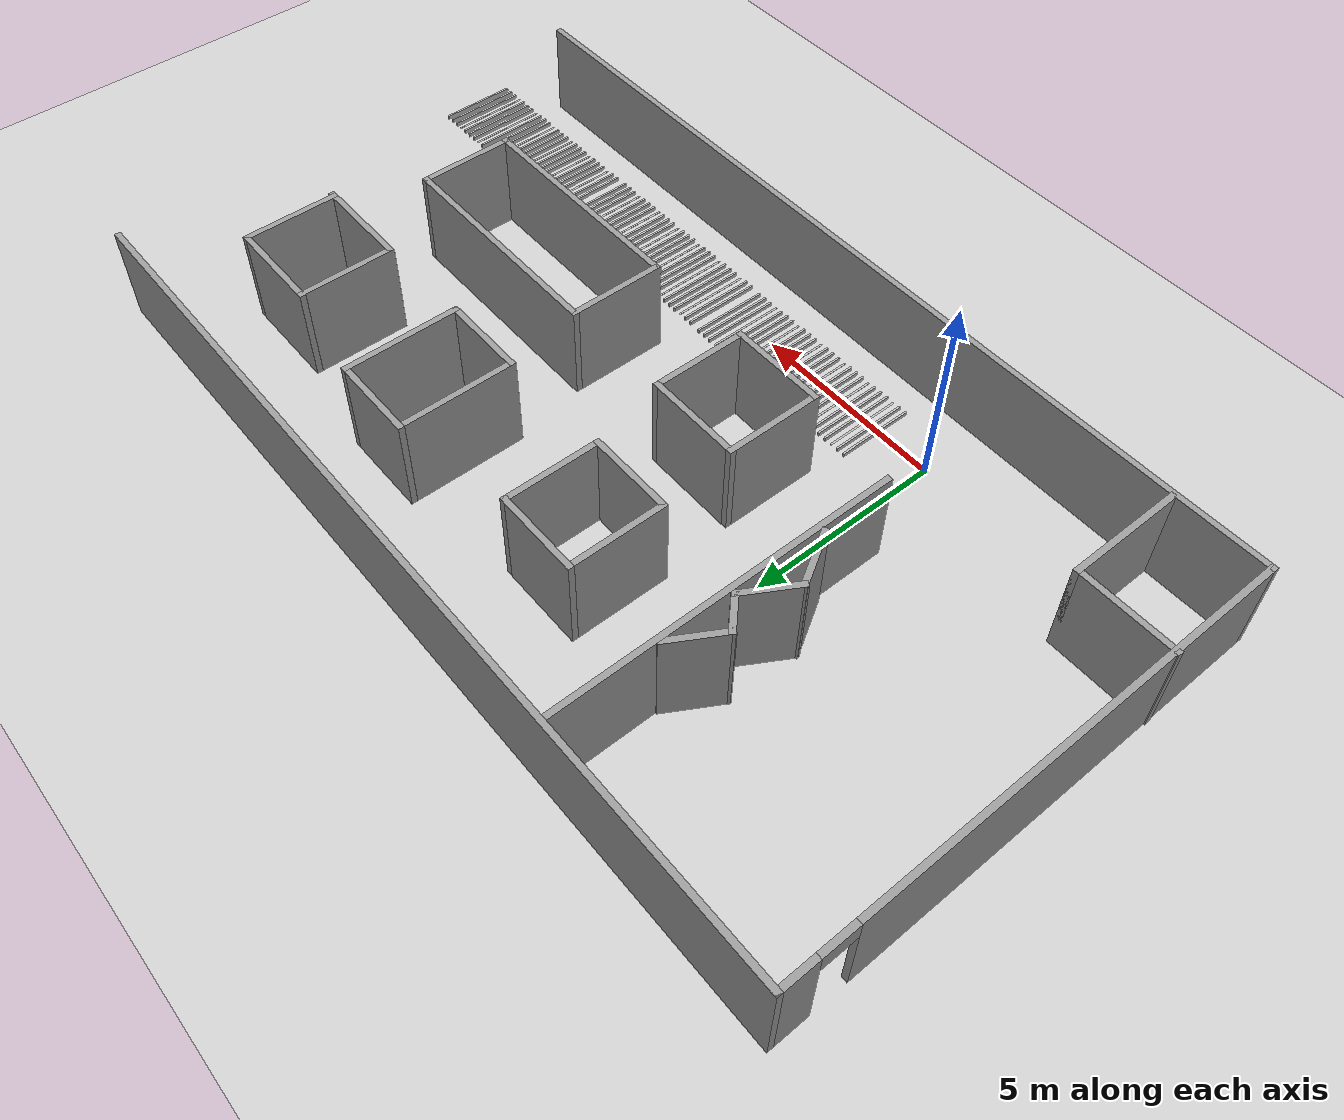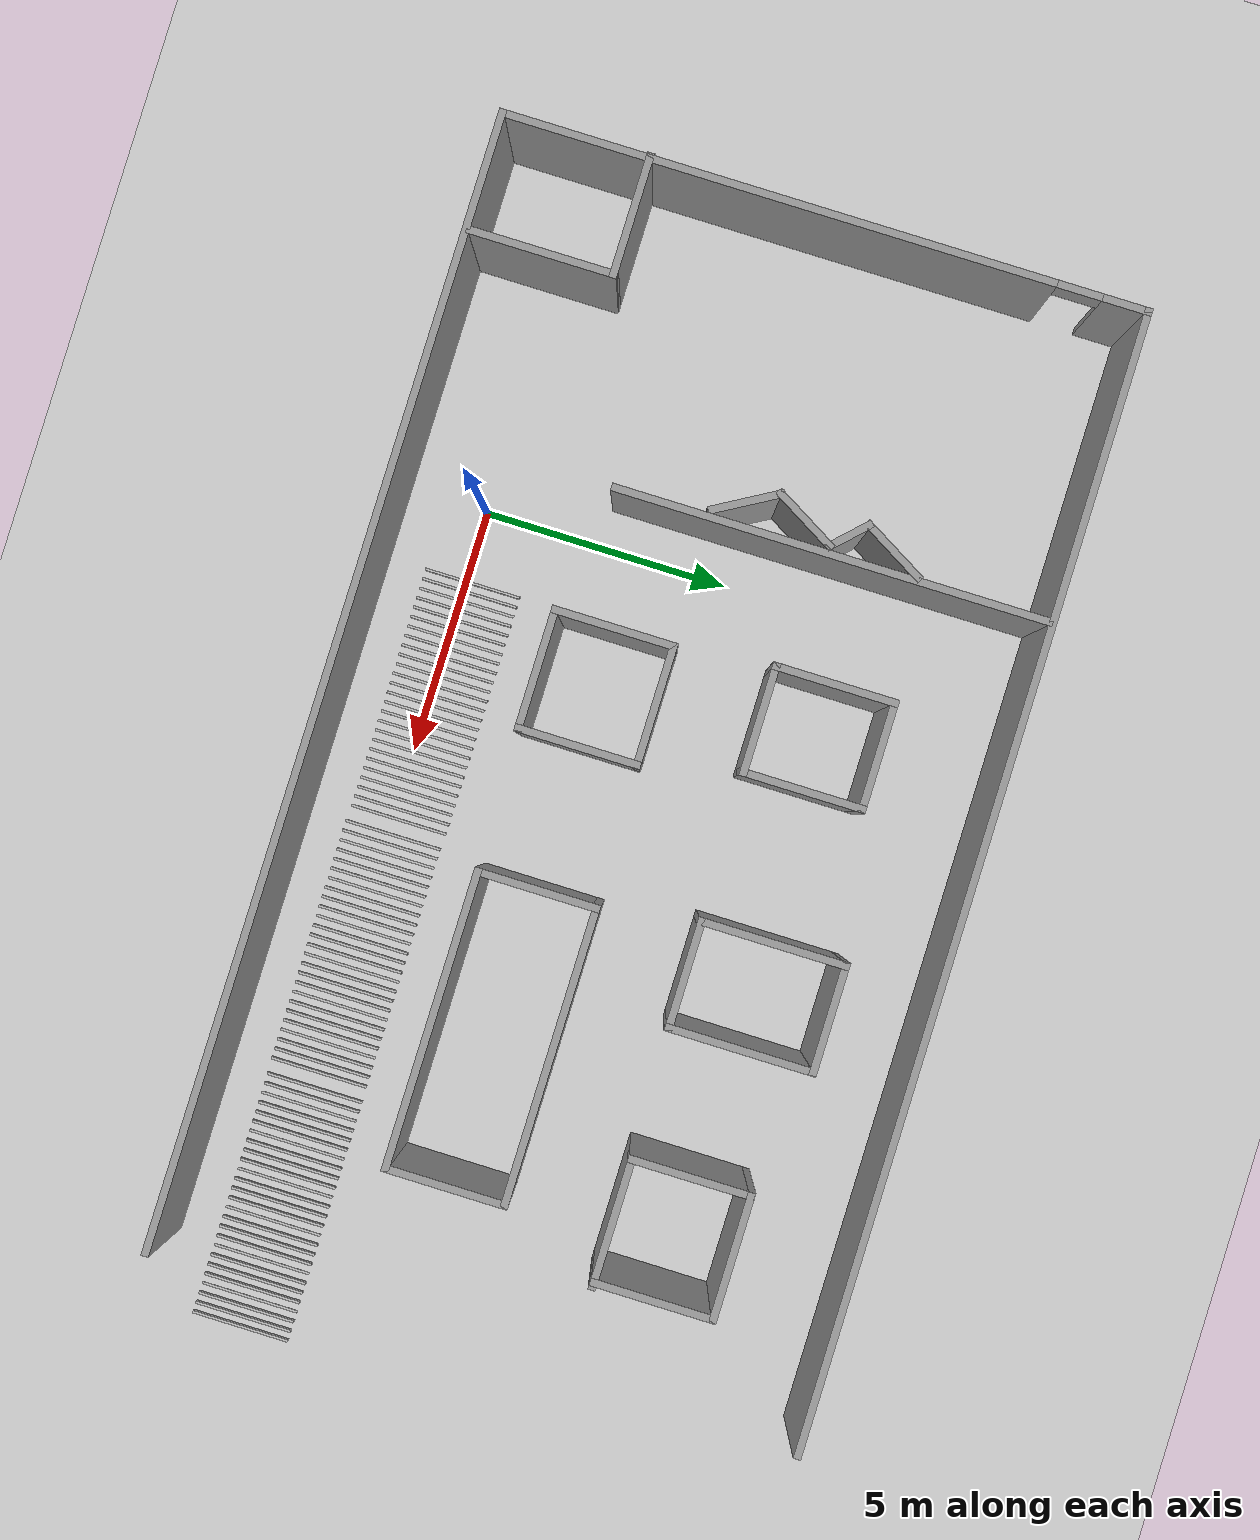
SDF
<sdf version="1.7">
 <world name="default">
  <light name="sun" type="directional">
   <pose>0 0 10 0 -0 0</pose>
   <diffuse>0.8 0.8 0.8 1</diffuse>
   <specular>0.2 0.2 0.2 1</specular>
   <attenuation>
    <range>1000</range>
    <constant>0.9</constant>
    <linear>0.01</linear>
    <quadratic>0.001</quadratic>
   </attenuation>
   <direction>-0.5 0.1 -0.9</direction>
   <spot><inner_angle>0</inner_angle><outer_angle>0</outer_angle><falloff>0</falloff></spot>
  </light>
  <model name="ground_plane">
   <static>1</static>
   <link name="link">
    <collision name="collision">
     <geometry><plane><normal>0 0 1</normal><size>100 100</size></plane></geometry>
     <surface>
      <contact><collide_bitmask>65535</collide_bitmask></contact>
      <friction><ode><mu>100</mu><mu2>50</mu2></ode></friction>
     </surface>
    </collision>
    <visual name="visual">
     <cast_shadows>0</cast_shadows>
     <geometry><plane><normal>0 0 1</normal><size>100 100</size></plane></geometry>
     <material>
      <script><uri>file://media/materials/scripts/gazebo.material</uri><name>Gazebo/Grey</name></script>
     </material>
    </visual>
   </link>
  </model>
  <gravity>0 0 -9.8</gravity>
  <magnetic_field>6e-06 2.3e-05 -4.2e-05</magnetic_field>
  <atmosphere type="adiabatic"/>
  <physics type="ode">
   <max_step_size>0.001</max_step_size>
   <real_time_factor>1</real_time_factor>
   <real_time_update_rate>1000</real_time_update_rate>
  </physics>
  <scene><ambient>0.4 0.4 0.4 1</ambient><background>0.7 0.7 0.7 1</background><shadows>1</shadows></scene>
  <spherical_coordinates>
   <surface_model>EARTH_WGS84</surface_model>
   <latitude_deg>0</latitude_deg>
   <longitude_deg>0</longitude_deg>
   <elevation>0</elevation>
   <heading_deg>0</heading_deg>
  </spherical_coordinates>
  <model name="office.world">
   <pose>4.21705 4.72731 0 0 -0 0</pose>
   <link name="Wall_11">
    <collision name="Wall_11_Collision">
     <geometry><box><size>22.75 0.15 2.5</size></box></geometry>
     <pose>0 0 1.25 0 -0 0</pose>
    </collision>
    <visual name="Wall_11_Visual">
     <pose>0 0 1.25 0 -0 0</pose>
     <geometry><box><size>22.75 0.15 2.5</size></box></geometry>
     <material>
      <script><uri>file://media/materials/scripts/gazebo.material</uri><name>Gazebo/Grey</name></script>
      <ambient>1 1 1 1</ambient>
     </material>
     <meta><layer>0</layer></meta>
    </visual>
    <pose>0.015161 6.425 0 0 -0 3.14159</pose>
   </link>
   <link name="Wall_15">
    <collision name="Wall_15_Collision">
     <geometry><box><size>8.75 0.15 2.5</size></box></geometry>
     <pose>0 0 1.25 0 -0 0</pose>
    </collision>
    <visual name="Wall_15_Visual">
     <pose>0 0 1.25 0 -0 0</pose>
     <geometry><box><size>8.75 0.15 2.5</size></box></geometry>
     <material>
      <script><uri>file://media/materials/scripts/gazebo.material</uri><name>Gazebo/Grey</name></script>
      <ambient>1 1 1 1</ambient>
     </material>
     <meta><layer>0</layer></meta>
    </visual>
    <pose>-5.08854 2.04563 0 0 -0 -1.5708</pose>
   </link>
   <link name="Wall_17">
    <collision name="Wall_17_Collision">
     <geometry><box><size>2.5 0.15 2.5</size></box></geometry>
     <pose>0 0 1.25 0 -0 0</pose>
    </collision>
    <visual name="Wall_17_Visual">
     <pose>0 0 1.25 0 -0 0</pose>
     <geometry><box><size>2.5 0.15 2.5</size></box></geometry>
     <material>
      <script><uri>file://media/materials/scripts/gazebo.material</uri><name>Gazebo/Grey</name></script>
      <ambient>1 1 1 1</ambient>
     </material>
     <meta><layer>0</layer></meta>
    </visual>
    <pose>-2.75356 2.83565 0 0 -0 -1.5708</pose>
   </link>
   <link name="Wall_18">
    <collision name="Wall_18_Collision">
     <geometry><box><size>2.25 0.15 2.5</size></box></geometry>
     <pose>0 0 1.25 0 -0 0</pose>
    </collision>
    <visual name="Wall_18_Visual">
     <pose>0 0 1.25 0 -0 0</pose>
     <geometry><box><size>2.25 0.15 2.5</size></box></geometry>
     <material>
      <script><uri>file://media/materials/scripts/gazebo.material</uri><name>Gazebo/Grey</name></script>
      <ambient>1 1 1 1</ambient>
     </material>
     <meta><layer>0</layer></meta>
    </visual>
    <pose>-1.70356 1.66065 0 0 -0 0</pose>
   </link>
   <link name="Wall_19">
    <collision name="Wall_19_Collision">
     <geometry><box><size>2.5 0.15 2.5</size></box></geometry>
     <pose>0 0 1.25 0 -0 0</pose>
    </collision>
    <visual name="Wall_19_Visual">
     <pose>0 0 1.25 0 -0 0</pose>
     <geometry><box><size>2.5 0.15 2.5</size></box></geometry>
     <material>
      <script><uri>file://media/materials/scripts/gazebo.material</uri><name>Gazebo/Grey</name></script>
      <ambient>1 1 1 1</ambient>
     </material>
     <meta><layer>0</layer></meta>
    </visual>
    <pose>-0.653558 2.83565 0 0 -0 1.5708</pose>
   </link>
   <link name="Wall_20">
    <collision name="Wall_20_Collision">
     <geometry><box><size>2.25 0.15 2.5</size></box></geometry>
     <pose>0 0 1.25 0 -0 0</pose>
    </collision>
    <visual name="Wall_20_Visual">
     <pose>0 0 1.25 0 -0 0</pose>
     <geometry><box><size>2.25 0.15 2.5</size></box></geometry>
     <material>
      <script><uri>file://media/materials/scripts/gazebo.material</uri><name>Gazebo/Grey</name></script>
      <ambient>1 1 1 1</ambient>
     </material>
     <meta><layer>0</layer></meta>
    </visual>
    <pose>-1.70356 4.01065 0 0 -0 3.14159</pose>
   </link>
   <link name="Wall_22">
    <collision name="Wall_22_Collision">
     <geometry><box><size>3 0.15 2.5</size></box></geometry>
     <pose>0 0 1.25 0 -0 0</pose>
    </collision>
    <visual name="Wall_22_Visual">
     <pose>0 0 1.25 0 -0 0</pose>
     <geometry><box><size>3 0.15 2.5</size></box></geometry>
     <material>
      <script><uri>file://media/materials/scripts/gazebo.material</uri><name>Gazebo/Grey</name></script>
      <ambient>1 1 1 1</ambient>
     </material>
     <meta><layer>0</layer></meta>
    </visual>
    <pose>2.27019 3.1611 0 0 -0 -1.5708</pose>
   </link>
   <link name="Wall_23">
    <collision name="Wall_23_Collision">
     <geometry><box><size>2.25 0.15 2.5</size></box></geometry>
     <pose>0 0 1.25 0 -0 0</pose>
    </collision>
    <visual name="Wall_23_Visual">
     <pose>0 0 1.25 0 -0 0</pose>
     <geometry><box><size>2.25 0.15 2.5</size></box></geometry>
     <material>
      <script><uri>file://media/materials/scripts/gazebo.material</uri><name>Gazebo/Grey</name></script>
      <ambient>1 1 1 1</ambient>
     </material>
     <meta><layer>0</layer></meta>
    </visual>
    <pose>3.32019 1.7361 0 0 -0 0</pose>
   </link>
   <link name="Wall_24">
    <collision name="Wall_24_Collision">
     <geometry><box><size>3 0.15 2.5</size></box></geometry>
     <pose>0 0 1.25 0 -0 0</pose>
    </collision>
    <visual name="Wall_24_Visual">
     <pose>0 0 1.25 0 -0 0</pose>
     <geometry><box><size>3 0.15 2.5</size></box></geometry>
     <material>
      <script><uri>file://media/materials/scripts/gazebo.material</uri><name>Gazebo/Grey</name></script>
      <ambient>1 1 1 1</ambient>
     </material>
     <meta><layer>0</layer></meta>
    </visual>
    <pose>4.37019 3.1611 0 0 -0 1.5708</pose>
   </link>
   <link name="Wall_25">
    <collision name="Wall_25_Collision">
     <geometry><box><size>2.25 0.15 2.5</size></box></geometry>
     <pose>0 0 1.25 0 -0 0</pose>
    </collision>
    <visual name="Wall_25_Visual">
     <pose>0 0 1.25 0 -0 0</pose>
     <geometry><box><size>2.25 0.15 2.5</size></box></geometry>
     <material>
      <script><uri>file://media/materials/scripts/gazebo.material</uri><name>Gazebo/Grey</name></script>
      <ambient>1 1 1 1</ambient>
     </material>
     <meta><layer>0</layer></meta>
    </visual>
    <pose>3.32019 4.5861 0 0 -0 3.14159</pose>
   </link>
   <link name="Wall_27">
    <collision name="Wall_27_Collision">
     <geometry><box><size>2.5 0.15 2.5</size></box></geometry>
     <pose>0 0 1.25 0 -0 0</pose>
    </collision>
    <visual name="Wall_27_Visual">
     <pose>0 0 1.25 0 -0 0</pose>
     <geometry><box><size>2.5 0.15 2.5</size></box></geometry>
     <material>
      <script><uri>file://media/materials/scripts/gazebo.material</uri><name>Gazebo/Grey</name></script>
      <ambient>1 1 1 1</ambient>
     </material>
     <meta><layer>0</layer></meta>
    </visual>
    <pose>6.94016 2.97716 0 0 -0 -1.5708</pose>
   </link>
   <link name="Wall_28">
    <collision name="Wall_28_Collision">
     <geometry><box><size>2.64151 0.15 2.5</size></box></geometry>
     <pose>0 0 1.25 0 -0 0</pose>
    </collision>
    <visual name="Wall_28_Visual">
     <pose>0 0 1.25 0 -0 0</pose>
     <geometry><box><size>2.64151 0.15 2.5</size></box></geometry>
     <material>
      <script><uri>file://media/materials/scripts/gazebo.material</uri><name>Gazebo/Grey</name></script>
      <ambient>1 1 1 1</ambient>
     </material>
     <meta><layer>0</layer></meta>
    </visual>
    <pose>8.18592 1.80216 0 0 -0 0</pose>
   </link>
   <link name="Wall_29">
    <collision name="Wall_29_Collision">
     <geometry><box><size>2.5 0.15 2.5</size></box></geometry>
     <pose>0 0 1.25 0 -0 0</pose>
    </collision>
    <visual name="Wall_29_Visual">
     <pose>0 0 1.25 0 -0 0</pose>
     <geometry><box><size>2.5 0.15 2.5</size></box></geometry>
     <material>
      <script><uri>file://media/materials/scripts/gazebo.material</uri><name>Gazebo/Grey</name></script>
      <ambient>1 1 1 1</ambient>
     </material>
     <meta><layer>0</layer></meta>
    </visual>
    <pose>9.36092 2.97716 0 0 -0 1.5708</pose>
   </link>
   <link name="Wall_30">
    <collision name="Wall_30_Collision">
     <geometry><box><size>2.57076 0.15 2.5</size></box></geometry>
     <pose>0 0 1.25 0 -0 0</pose>
    </collision>
    <visual name="Wall_30_Visual">
     <pose>0 0 1.25 0 -0 0</pose>
     <geometry><box><size>2.57076 0.15 2.5</size></box></geometry>
     <material>
      <script><uri>file://media/materials/scripts/gazebo.material</uri><name>Gazebo/Grey</name></script>
      <ambient>1 1 1 1</ambient>
     </material>
     <meta><layer>0</layer></meta>
    </visual>
    <pose>8.15054 4.15216 0 0 -0 3.14159</pose>
   </link>
   <link name="Wall_32">
    <collision name="Wall_32_Collision">
     <geometry><box><size>2.5 0.15 2.5</size></box></geometry>
     <pose>0 0 1.25 0 -0 0</pose>
    </collision>
    <visual name="Wall_32_Visual">
     <pose>0 0 1.25 0 -0 0</pose>
     <geometry><box><size>2.5 0.15 2.5</size></box></geometry>
     <material>
      <script><uri>file://media/materials/scripts/gazebo.material</uri><name>Gazebo/Grey</name></script>
      <ambient>1 1 1 1</ambient>
     </material>
     <meta><layer>0</layer></meta>
    </visual>
    <pose>-2.54129 -1.48053 0 0 -0 -1.5708</pose>
   </link>
   <link name="Wall_33">
    <collision name="Wall_33_Collision">
     <geometry><box><size>2.5 0.15 2.5</size></box></geometry>
     <pose>0 0 1.25 0 -0 0</pose>
    </collision>
    <visual name="Wall_33_Visual">
     <pose>0 0 1.25 0 -0 0</pose>
     <geometry><box><size>2.5 0.15 2.5</size></box></geometry>
     <material>
      <script><uri>file://media/materials/scripts/gazebo.material</uri><name>Gazebo/Grey</name></script>
      <ambient>1 1 1 1</ambient>
     </material>
     <meta><layer>0</layer></meta>
    </visual>
    <pose>-1.36629 -2.65553 0 0 -0 0</pose>
   </link>
   <link name="Wall_34">
    <collision name="Wall_34_Collision">
     <geometry><box><size>2.5 0.15 2.5</size></box></geometry>
     <pose>0 0 1.25 0 -0 0</pose>
    </collision>
    <visual name="Wall_34_Visual">
     <pose>0 0 1.25 0 -0 0</pose>
     <geometry><box><size>2.5 0.15 2.5</size></box></geometry>
     <material>
      <script><uri>file://media/materials/scripts/gazebo.material</uri><name>Gazebo/Grey</name></script>
      <ambient>1 1 1 1</ambient>
     </material>
     <meta><layer>0</layer></meta>
    </visual>
    <pose>-0.191286 -1.48053 0 0 -0 1.5708</pose>
   </link>
   <link name="Wall_35">
    <collision name="Wall_35_Collision">
     <geometry><box><size>2.5 0.15 2.5</size></box></geometry>
     <pose>0 0 1.25 0 -0 0</pose>
    </collision>
    <visual name="Wall_35_Visual">
     <pose>0 0 1.25 0 -0 0</pose>
     <geometry><box><size>2.5 0.15 2.5</size></box></geometry>
     <material>
      <script><uri>file://media/materials/scripts/gazebo.material</uri><name>Gazebo/Grey</name></script>
      <ambient>1 1 1 1</ambient>
     </material>
     <meta><layer>0</layer></meta>
    </visual>
    <pose>-1.36629 -0.305535 0 0 -0 3.14159</pose>
   </link>
   <link name="Wall_37">
    <collision name="Wall_37_Collision">
     <geometry><box><size>2.5 0.15 2.5</size></box></geometry>
     <pose>0 0 1.25 0 -0 0</pose>
    </collision>
    <visual name="Wall_37_Visual">
     <pose>0 0 1.25 0 -0 0</pose>
     <geometry><box><size>2.5 0.15 2.5</size></box></geometry>
     <material>
      <script><uri>file://media/materials/scripts/gazebo.material</uri><name>Gazebo/Grey</name></script>
      <ambient>1 1 1 1</ambient>
     </material>
     <meta><layer>0</layer></meta>
    </visual>
    <pose>2.62398 -1.40978 0 0 -0 -1.5708</pose>
   </link>
   <link name="Wall_38">
    <collision name="Wall_38_Collision">
     <geometry><box><size>6 0.15 2.5</size></box></geometry>
     <pose>0 0 1.25 0 -0 0</pose>
    </collision>
    <visual name="Wall_38_Visual">
     <pose>0 0 1.25 0 -0 0</pose>
     <geometry><box><size>6 0.15 2.5</size></box></geometry>
     <material>
      <script><uri>file://media/materials/scripts/gazebo.material</uri><name>Gazebo/Grey</name></script>
      <ambient>1 1 1 1</ambient>
     </material>
     <meta><layer>0</layer></meta>
    </visual>
    <pose>5.54898 -2.58478 0 0 -0 0</pose>
   </link>
   <link name="Wall_39">
    <collision name="Wall_39_Collision">
     <geometry><box><size>2.5 0.15 2.5</size></box></geometry>
     <pose>0 0 1.25 0 -0 0</pose>
    </collision>
    <visual name="Wall_39_Visual">
     <pose>0 0 1.25 0 -0 0</pose>
     <geometry><box><size>2.5 0.15 2.5</size></box></geometry>
     <material>
      <script><uri>file://media/materials/scripts/gazebo.material</uri><name>Gazebo/Grey</name></script>
      <ambient>1 1 1 1</ambient>
     </material>
     <meta><layer>0</layer></meta>
    </visual>
    <pose>8.47398 -1.40978 0 0 -0 1.5708</pose>
   </link>
   <link name="Wall_40">
    <collision name="Wall_40_Collision">
     <geometry><box><size>6 0.15 2.5</size></box></geometry>
     <pose>0 0 1.25 0 -0 0</pose>
    </collision>
    <visual name="Wall_40_Visual">
     <pose>0 0 1.25 0 -0 0</pose>
     <geometry><box><size>6 0.15 2.5</size></box></geometry>
     <material>
      <script><uri>file://media/materials/scripts/gazebo.material</uri><name>Gazebo/Grey</name></script>
      <ambient>1 1 1 1</ambient>
     </material>
     <meta><layer>0</layer></meta>
    </visual>
    <pose>5.54898 -0.234777 0 0 -0 3.14159</pose>
   </link>
   <link name="Wall_42">
    <collision name="Wall_42_Collision">
     <geometry><box><size>1.5 0.15 2.5</size></box></geometry>
     <pose>0 0 1.25 0 -0 0</pose>
    </collision>
    <visual name="Wall_42_Visual">
     <pose>0 0 1.25 0 -0 0</pose>
     <geometry><box><size>1.5 0.15 2.5</size></box></geometry>
     <material>
      <script><uri>file://media/materials/scripts/gazebo.material</uri><name>Gazebo/Grey</name></script>
      <ambient>1 1 1 1</ambient>
     </material>
     <meta><layer>0</layer></meta>
    </visual>
    <pose>-5.4968 3.14305 0 0 -0 -2.0944</pose>
   </link>
   <link name="Wall_43">
    <collision name="Wall_43_Collision">
     <geometry><box><size>1 0.15 2.5</size></box></geometry>
     <pose>0 0 1.25 0 -0 0</pose>
    </collision>
    <visual name="Wall_43_Visual">
     <pose>0 0 1.25 0 -0 0</pose>
     <geometry><box><size>1 0.15 2.5</size></box></geometry>
     <material>
      <script><uri>file://media/materials/scripts/gazebo.material</uri><name>Gazebo/Grey</name></script>
      <ambient>1 1 1 1</ambient>
     </material>
     <meta><layer>0</layer></meta>
    </visual>
    <pose>-5.53378 2.25796 0 0 -0 -0.785398</pose>
   </link>
   <link name="Wall_44">
    <collision name="Wall_44_Collision">
     <geometry><box><size>1.5 0.15 2.5</size></box></geometry>
     <pose>0 0 1.25 0 -0 0</pose>
    </collision>
    <visual name="Wall_44_Visual">
     <pose>0 0 1.25 0 -0 0</pose>
     <geometry><box><size>1.5 0.15 2.5</size></box></geometry>
     <material>
      <script><uri>file://media/materials/scripts/gazebo.material</uri><name>Gazebo/Grey</name></script>
      <ambient>1 1 1 1</ambient>
     </material>
     <meta><layer>0</layer></meta>
    </visual>
    <pose>-5.57076 1.37288 0 0 -0 -2.0944</pose>
   </link>
   <link name="Wall_45">
    <collision name="Wall_45_Collision">
     <geometry><box><size>1.5 0.15 2.5</size></box></geometry>
     <pose>0 0 1.25 0 -0 0</pose>
    </collision>
    <visual name="Wall_45_Visual">
     <pose>0 0 1.25 0 -0 0</pose>
     <geometry><box><size>1.5 0.15 2.5</size></box></geometry>
     <material>
      <script><uri>file://media/materials/scripts/gazebo.material</uri><name>Gazebo/Grey</name></script>
      <ambient>1 1 1 1</ambient>
     </material>
     <meta><layer>0</layer></meta>
    </visual>
    <pose>-5.57076 0.203741 0 0 -0 -1.0472</pose>
   </link>
   <link name="Wall_47">
    <collision name="Wall_47_Collision">
     <geometry><box><size>2.5 0.15 2.5</size></box></geometry>
     <pose>0 0 1.25 0 -0 0</pose>
    </collision>
    <visual name="Wall_47_Visual">
     <pose>0 0 1.25 0 -0 0</pose>
     <geometry><box><size>2.5 0.15 2.5</size></box></geometry>
     <material>
      <script><uri>file://media/materials/scripts/gazebo.material</uri><name>Gazebo/Grey</name></script>
      <ambient>1 1 1 1</ambient>
     </material>
     <meta><layer>0</layer></meta>
    </visual>
    <pose>-10.1402 -3.4896 0 0 -0 0</pose>
   </link>
   <link name="Wall_48">
    <collision name="Wall_48_Collision">
     <geometry><box><size>3 0.15 2.5</size></box></geometry>
     <pose>0 0 1.25 0 -0 0</pose>
    </collision>
    <visual name="Wall_48_Visual">
     <pose>0 0 1.25 0 -0 0</pose>
     <geometry><box><size>3 0.15 2.5</size></box></geometry>
     <material>
      <script><uri>file://media/materials/scripts/gazebo.material</uri><name>Gazebo/Grey</name></script>
      <ambient>1 1 1 1</ambient>
     </material>
     <meta><layer>0</layer></meta>
    </visual>
    <pose>-8.96516 -4.9146 0 0 -0 -1.5708</pose>
   </link>
   <link name="Wall_8">
    <pose>-11.2848 -0 0 0 -0 -1.5708</pose>
    <visual name="Wall_8_Visual_0">
     <pose>-6.011 0 1.25 0 -0 0</pose>
     <geometry><box><size>0.977998 0.15 2.5</size></box></geometry>
     <material>
      <script><uri>file://media/materials/scripts/gazebo.material</uri><name>Gazebo/Grey</name></script>
      <ambient>1 1 1 1</ambient>
     </material>
     <meta><layer>0</layer></meta>
    </visual>
    <collision name="Wall_8_Collision_0">
     <geometry><box><size>0.977998 0.15 2.5</size></box></geometry>
     <pose>-6.011 0 1.25 0 -0 0</pose>
    </collision>
    <visual name="Wall_8_Visual_1">
     <pose>0.938999 0 1.25 0 -0 0</pose>
     <geometry><box><size>11.122 0.15 2.5</size></box></geometry>
     <material>
      <script><uri>file://media/materials/scripts/gazebo.material</uri><name>Gazebo/Grey</name></script>
      <ambient>1 1 1 1</ambient>
     </material>
     <meta><layer>0</layer></meta>
    </visual>
    <collision name="Wall_8_Collision_1">
     <geometry><box><size>11.122 0.15 2.5</size></box></geometry>
     <pose>0.938999 0 1.25 0 -0 0</pose>
    </collision>
    <visual name="Wall_8_Visual_2">
     <pose>-5.072 0 2.25 0 -0 0</pose>
     <geometry><box><size>0.9 0.15 0.5</size></box></geometry>
     <material>
      <script><uri>file://media/materials/scripts/gazebo.material</uri><name>Gazebo/Grey</name></script>
      <ambient>1 1 1 1</ambient>
     </material>
     <meta><layer>0</layer></meta>
    </visual>
    <collision name="Wall_8_Collision_2">
     <geometry><box><size>0.9 0.15 0.5</size></box></geometry>
     <pose>-5.072 0 2.25 0 -0 0</pose>
    </collision>
   </link>
   <link name="Wall_9">
    <collision name="Wall_9_Collision">
     <geometry><box><size>22.75 0.15 2.5</size></box></geometry>
     <pose>0 0 1.25 0 -0 0</pose>
    </collision>
    <visual name="Wall_9_Visual">
     <pose>0 0 1.25 0 -0 0</pose>
     <geometry><box><size>22.75 0.15 2.5</size></box></geometry>
     <material>
      <script><uri>file://media/materials/scripts/gazebo.material</uri><name>Gazebo/Grey</name></script>
      <ambient>1 1 1 1</ambient>
     </material>
     <meta><layer>0</layer></meta>
    </visual>
    <pose>0.015161 -6.425 0 0 -0 0</pose>
   </link>
   <static>1</static>
  </model>
  <model name="my_model">
   <link name="bot_wall0">
    <visual name="visual">
     <geometry><box><size>0.05 2 0.1</size></box></geometry>
     <material><script><uri>model://hallway/materials/scripts</uri><name>feature_3</name></script></material>
    </visual>
    <collision name="collision"><geometry><box><size>0.05 2 0.1</size></box></geometry></collision>
    <inertial>
     <inertia><ixx>1</ixx><ixy>0</ixy><ixz>0</ixz><iyy>1</iyy><iyz>0</iyz><izz>1</izz></inertia>
     <mass>1</mass>
    </inertial>
   </link>
   <link name="bot_wall1">
    <pose>0.2 0 0 0 -0 0</pose>
    <visual name="visual">
     <geometry><box><size>0.05 2 0.1</size></box></geometry>
     <material><script><uri>model://hallway/materials/scripts</uri><name>feature_3</name></script></material>
    </visual>
    <collision name="collision"><geometry><box><size>0.05 2 0.1</size></box></geometry></collision>
    <inertial>
     <inertia><ixx>1</ixx><ixy>0</ixy><ixz>0</ixz><iyy>1</iyy><iyz>0</iyz><izz>1</izz></inertia>
     <mass>1</mass>
    </inertial>
   </link>
   <link name="bot_wall2">
    <pose>0.4 0 0 0 -0 0</pose>
    <visual name="visual">
     <geometry><box><size>0.05 2 0.01</size></box></geometry>
     <material><script><uri>model://hallway/materials/scripts</uri><name>feature_3</name></script></material>
    </visual>
    <collision name="collision"><geometry><box><size>0.05 2 0.01</size></box></geometry></collision>
    <inertial>
     <inertia><ixx>1</ixx><ixy>0</ixy><ixz>0</ixz><iyy>1</iyy><iyz>0</iyz><izz>1</izz></inertia>
     <mass>1</mass>
    </inertial>
   </link>
   <link name="bot_wall3">
    <pose>0.6 0 0 0 -0 0</pose>
    <visual name="visual">
     <geometry><box><size>0.05 2 0.1</size></box></geometry>
     <material><script><uri>model://hallway/materials/scripts</uri><name>feature_3</name></script></material>
    </visual>
    <collision name="collision"><geometry><box><size>0.05 2 0.1</size></box></geometry></collision>
    <inertial>
     <inertia><ixx>1</ixx><ixy>0</ixy><ixz>0</ixz><iyy>1</iyy><iyz>0</iyz><izz>1</izz></inertia>
     <mass>1</mass>
    </inertial>
   </link>
   <link name="bot_wall4">
    <pose>0.8 0 0 0 -0 0</pose>
    <visual name="visual">
     <geometry><box><size>0.05 2 0.1</size></box></geometry>
     <material><script><uri>model://hallway/materials/scripts</uri><name>feature_3</name></script></material>
    </visual>
    <collision name="collision"><geometry><box><size>0.05 2 0.1</size></box></geometry></collision>
    <inertial>
     <inertia><ixx>1</ixx><ixy>0</ixy><ixz>0</ixz><iyy>1</iyy><iyz>0</iyz><izz>1</izz></inertia>
     <mass>1</mass>
    </inertial>
   </link>
   <link name="bot_wall5">
    <pose>1 0 0 0 -0 0</pose>
    <visual name="visual">
     <geometry><box><size>0.05 2 0.1</size></box></geometry>
     <material><script><uri>model://hallway/materials/scripts</uri><name>feature_3</name></script></material>
    </visual>
    <collision name="collision"><geometry><box><size>0.05 2 0.1</size></box></geometry></collision>
    <inertial>
     <inertia><ixx>1</ixx><ixy>0</ixy><ixz>0</ixz><iyy>1</iyy><iyz>0</iyz><izz>1</izz></inertia>
     <mass>1</mass>
    </inertial>
   </link>
   <link name="bot_wall6">
    <pose>1.2 0 0 0 -0 0</pose>
    <visual name="visual">
     <geometry><box><size>0.05 2 0.01</size></box></geometry>
     <material><script><uri>model://hallway/materials/scripts</uri><name>feature_3</name></script></material>
    </visual>
    <collision name="collision"><geometry><box><size>0.05 2 0.01</size></box></geometry></collision>
    <inertial>
     <inertia><ixx>1</ixx><ixy>0</ixy><ixz>0</ixz><iyy>1</iyy><iyz>0</iyz><izz>1</izz></inertia>
     <mass>1</mass>
    </inertial>
   </link>
   <link name="bot_wall7">
    <pose>1.4 0 0 0 -0 0</pose>
    <visual name="visual">
     <geometry><box><size>0.05 2 0.1</size></box></geometry>
     <material><script><uri>model://hallway/materials/scripts</uri><name>feature_3</name></script></material>
    </visual>
    <collision name="collision"><geometry><box><size>0.05 2 0.1</size></box></geometry></collision>
    <inertial>
     <inertia><ixx>1</ixx><ixy>0</ixy><ixz>0</ixz><iyy>1</iyy><iyz>0</iyz><izz>1</izz></inertia>
     <mass>1</mass>
    </inertial>
   </link>
   <link name="bot_wall8">
    <pose>1.6 0 0 0 -0 0</pose>
    <visual name="visual">
     <geometry><box><size>0.05 2 0.1</size></box></geometry>
     <material><script><uri>model://hallway/materials/scripts</uri><name>feature_3</name></script></material>
    </visual>
    <collision name="collision"><geometry><box><size>0.05 2 0.1</size></box></geometry></collision>
    <inertial>
     <inertia><ixx>1</ixx><ixy>0</ixy><ixz>0</ixz><iyy>1</iyy><iyz>0</iyz><izz>1</izz></inertia>
     <mass>1</mass>
    </inertial>
   </link>
   <link name="bot_wall9">
    <pose>1.8 0 0 0 -0 0</pose>
    <visual name="visual">
     <geometry><box><size>0.05 2 0.1</size></box></geometry>
     <material><script><uri>model://hallway/materials/scripts</uri><name>feature_3</name></script></material>
    </visual>
    <collision name="collision"><geometry><box><size>0.05 2 0.1</size></box></geometry></collision>
    <inertial>
     <inertia><ixx>1</ixx><ixy>0</ixy><ixz>0</ixz><iyy>1</iyy><iyz>0</iyz><izz>1</izz></inertia>
     <mass>1</mass>
    </inertial>
   </link>
   <link name="bot_wall10">
    <pose>2 0 0 0 -0 0</pose>
    <visual name="visual">
     <geometry><box><size>0.05 2 0.01</size></box></geometry>
     <material><script><uri>model://hallway/materials/scripts</uri><name>feature_3</name></script></material>
    </visual>
    <collision name="collision"><geometry><box><size>0.05 2 0.01</size></box></geometry></collision>
    <inertial>
     <inertia><ixx>1</ixx><ixy>0</ixy><ixz>0</ixz><iyy>1</iyy><iyz>0</iyz><izz>1</izz></inertia>
     <mass>1</mass>
    </inertial>
   </link>
   <link name="bot_wall11">
    <pose>2.2 0 0 0 -0 0</pose>
    <visual name="visual">
     <geometry><box><size>0.05 2 0.1</size></box></geometry>
     <material><script><uri>model://hallway/materials/scripts</uri><name>feature_3</name></script></material>
    </visual>
    <collision name="collision"><geometry><box><size>0.05 2 0.1</size></box></geometry></collision>
    <inertial>
     <inertia><ixx>1</ixx><ixy>0</ixy><ixz>0</ixz><iyy>1</iyy><iyz>0</iyz><izz>1</izz></inertia>
     <mass>1</mass>
    </inertial>
   </link>
   <link name="bot_wall12">
    <pose>2.4 0 0 0 -0 0</pose>
    <visual name="visual">
     <geometry><box><size>0.05 2 0.1</size></box></geometry>
     <material><script><uri>model://hallway/materials/scripts</uri><name>feature_3</name></script></material>
    </visual>
    <collision name="collision"><geometry><box><size>0.05 2 0.1</size></box></geometry></collision>
    <inertial>
     <inertia><ixx>1</ixx><ixy>0</ixy><ixz>0</ixz><iyy>1</iyy><iyz>0</iyz><izz>1</izz></inertia>
     <mass>1</mass>
    </inertial>
   </link>
   <link name="bot_wall13">
    <pose>2.6 0 0 0 -0 0</pose>
    <visual name="visual">
     <geometry><box><size>0.05 2 0.1</size></box></geometry>
     <material><script><uri>model://hallway/materials/scripts</uri><name>feature_3</name></script></material>
    </visual>
    <collision name="collision"><geometry><box><size>0.05 2 0.1</size></box></geometry></collision>
    <inertial>
     <inertia><ixx>1</ixx><ixy>0</ixy><ixz>0</ixz><iyy>1</iyy><iyz>0</iyz><izz>1</izz></inertia>
     <mass>1</mass>
    </inertial>
   </link>
   <link name="bot_wall14">
    <pose>2.8 0 0 0 -0 0</pose>
    <visual name="visual">
     <geometry><box><size>0.05 2 0.01</size></box></geometry>
     <material><script><uri>model://hallway/materials/scripts</uri><name>feature_3</name></script></material>
    </visual>
    <collision name="collision"><geometry><box><size>0.05 2 0.01</size></box></geometry></collision>
    <inertial>
     <inertia><ixx>1</ixx><ixy>0</ixy><ixz>0</ixz><iyy>1</iyy><iyz>0</iyz><izz>1</izz></inertia>
     <mass>1</mass>
    </inertial>
   </link>
   <link name="bot_wall15">
    <pose>3 0 0 0 -0 0</pose>
    <visual name="visual">
     <geometry><box><size>0.05 2 0.1</size></box></geometry>
     <material><script><uri>model://hallway/materials/scripts</uri><name>feature_3</name></script></material>
    </visual>
    <collision name="collision"><geometry><box><size>0.05 2 0.1</size></box></geometry></collision>
    <inertial>
     <inertia><ixx>1</ixx><ixy>0</ixy><ixz>0</ixz><iyy>1</iyy><iyz>0</iyz><izz>1</izz></inertia>
     <mass>1</mass>
    </inertial>
   </link>
   <link name="bot_wall16">
    <pose>3.2 0 0 0 -0 0</pose>
    <visual name="visual">
     <geometry><box><size>0.05 2 0.1</size></box></geometry>
     <material><script><uri>model://hallway/materials/scripts</uri><name>feature_3</name></script></material>
    </visual>
    <collision name="collision"><geometry><box><size>0.05 2 0.1</size></box></geometry></collision>
    <inertial>
     <inertia><ixx>1</ixx><ixy>0</ixy><ixz>0</ixz><iyy>1</iyy><iyz>0</iyz><izz>1</izz></inertia>
     <mass>1</mass>
    </inertial>
   </link>
   <link name="bot_wall17">
    <pose>3.4 0 0 0 -0 0</pose>
    <visual name="visual">
     <geometry><box><size>0.05 2 0.1</size></box></geometry>
     <material><script><uri>model://hallway/materials/scripts</uri><name>feature_3</name></script></material>
    </visual>
    <collision name="collision"><geometry><box><size>0.05 2 0.1</size></box></geometry></collision>
    <inertial>
     <inertia><ixx>1</ixx><ixy>0</ixy><ixz>0</ixz><iyy>1</iyy><iyz>0</iyz><izz>1</izz></inertia>
     <mass>1</mass>
    </inertial>
   </link>
   <link name="bot_wall18">
    <pose>3.6 0 0 0 -0 0</pose>
    <visual name="visual">
     <geometry><box><size>0.05 2 0.01</size></box></geometry>
     <material><script><uri>model://hallway/materials/scripts</uri><name>feature_3</name></script></material>
    </visual>
    <collision name="collision"><geometry><box><size>0.05 2 0.01</size></box></geometry></collision>
    <inertial>
     <inertia><ixx>1</ixx><ixy>0</ixy><ixz>0</ixz><iyy>1</iyy><iyz>0</iyz><izz>1</izz></inertia>
     <mass>1</mass>
    </inertial>
   </link>
   <link name="bot_wall19">
    <pose>3.8 0 0 0 -0 0</pose>
    <visual name="visual">
     <geometry><box><size>0.05 2 0.1</size></box></geometry>
     <material><script><uri>model://hallway/materials/scripts</uri><name>feature_3</name></script></material>
    </visual>
    <collision name="collision"><geometry><box><size>0.05 2 0.1</size></box></geometry></collision>
    <inertial>
     <inertia><ixx>1</ixx><ixy>0</ixy><ixz>0</ixz><iyy>1</iyy><iyz>0</iyz><izz>1</izz></inertia>
     <mass>1</mass>
    </inertial>
   </link>
   <link name="bot_wall20">
    <pose>4 0 0 0 -0 0</pose>
    <visual name="visual">
     <geometry><box><size>0.05 2 0.1</size></box></geometry>
     <material><script><uri>model://hallway/materials/scripts</uri><name>feature_3</name></script></material>
    </visual>
    <collision name="collision"><geometry><box><size>0.05 2 0.1</size></box></geometry></collision>
    <inertial>
     <inertia><ixx>1</ixx><ixy>0</ixy><ixz>0</ixz><iyy>1</iyy><iyz>0</iyz><izz>1</izz></inertia>
     <mass>1</mass>
    </inertial>
   </link>
   <link name="bot_wall21">
    <pose>4.2 0 0 0 -0 0</pose>
    <visual name="visual">
     <geometry><box><size>0.05 2 0.1</size></box></geometry>
     <material><script><uri>model://hallway/materials/scripts</uri><name>feature_3</name></script></material>
    </visual>
    <collision name="collision"><geometry><box><size>0.05 2 0.1</size></box></geometry></collision>
    <inertial>
     <inertia><ixx>1</ixx><ixy>0</ixy><ixz>0</ixz><iyy>1</iyy><iyz>0</iyz><izz>1</izz></inertia>
     <mass>1</mass>
    </inertial>
   </link>
   <link name="bot_wall22">
    <pose>4.4 0 0 0 -0 0</pose>
    <visual name="visual">
     <geometry><box><size>0.05 2 0.01</size></box></geometry>
     <material><script><uri>model://hallway/materials/scripts</uri><name>feature_3</name></script></material>
    </visual>
    <collision name="collision"><geometry><box><size>0.05 2 0.01</size></box></geometry></collision>
    <inertial>
     <inertia><ixx>1</ixx><ixy>0</ixy><ixz>0</ixz><iyy>1</iyy><iyz>0</iyz><izz>1</izz></inertia>
     <mass>1</mass>
    </inertial>
   </link>
   <link name="bot_wall23">
    <pose>4.6 0 0 0 -0 0</pose>
    <visual name="visual">
     <geometry><box><size>0.05 2 0.1</size></box></geometry>
     <material><script><uri>model://hallway/materials/scripts</uri><name>feature_3</name></script></material>
    </visual>
    <collision name="collision"><geometry><box><size>0.05 2 0.1</size></box></geometry></collision>
    <inertial>
     <inertia><ixx>1</ixx><ixy>0</ixy><ixz>0</ixz><iyy>1</iyy><iyz>0</iyz><izz>1</izz></inertia>
     <mass>1</mass>
    </inertial>
   </link>
   <link name="bot_wall24">
    <pose>4.8 0 0 0 -0 0</pose>
    <visual name="visual">
     <geometry><box><size>0.05 2 0.1</size></box></geometry>
     <material><script><uri>model://hallway/materials/scripts</uri><name>feature_3</name></script></material>
    </visual>
    <collision name="collision"><geometry><box><size>0.05 2 0.1</size></box></geometry></collision>
    <inertial>
     <inertia><ixx>1</ixx><ixy>0</ixy><ixz>0</ixz><iyy>1</iyy><iyz>0</iyz><izz>1</izz></inertia>
     <mass>1</mass>
    </inertial>
   </link>
   <link name="bot_wall25">
    <pose>5 0 0 0 -0 0</pose>
    <visual name="visual">
     <geometry><box><size>0.05 2 0.1</size></box></geometry>
     <material><script><uri>model://hallway/materials/scripts</uri><name>feature_3</name></script></material>
    </visual>
    <collision name="collision"><geometry><box><size>0.05 2 0.1</size></box></geometry></collision>
    <inertial>
     <inertia><ixx>1</ixx><ixy>0</ixy><ixz>0</ixz><iyy>1</iyy><iyz>0</iyz><izz>1</izz></inertia>
     <mass>1</mass>
    </inertial>
   </link>
   <joint name="joint0" type="fixed"><parent>bot_wall0</parent><child>bot_wall1</child></joint>
   <joint name="joint1" type="fixed"><parent>bot_wall1</parent><child>bot_wall2</child></joint>
   <joint name="joint2" type="fixed"><parent>bot_wall2</parent><child>bot_wall3</child></joint>
   <joint name="joint3" type="fixed"><parent>bot_wall3</parent><child>bot_wall4</child></joint>
   <joint name="joint4" type="fixed"><parent>bot_wall4</parent><child>bot_wall5</child></joint>
   <joint name="joint5" type="fixed"><parent>bot_wall5</parent><child>bot_wall6</child></joint>
   <joint name="joint6" type="fixed"><parent>bot_wall6</parent><child>bot_wall7</child></joint>
   <joint name="joint7" type="fixed"><parent>bot_wall7</parent><child>bot_wall8</child></joint>
   <joint name="joint8" type="fixed"><parent>bot_wall8</parent><child>bot_wall9</child></joint>
   <joint name="joint9" type="fixed"><parent>bot_wall9</parent><child>bot_wall10</child></joint>
   <joint name="joint10" type="fixed"><parent>bot_wall10</parent><child>bot_wall11</child></joint>
   <joint name="joint11" type="fixed"><parent>bot_wall11</parent><child>bot_wall12</child></joint>
   <joint name="joint12" type="fixed"><parent>bot_wall12</parent><child>bot_wall13</child></joint>
   <joint name="joint13" type="fixed"><parent>bot_wall13</parent><child>bot_wall14</child></joint>
   <joint name="joint14" type="fixed"><parent>bot_wall14</parent><child>bot_wall15</child></joint>
   <joint name="joint15" type="fixed"><parent>bot_wall15</parent><child>bot_wall16</child></joint>
   <joint name="joint16" type="fixed"><parent>bot_wall16</parent><child>bot_wall17</child></joint>
   <joint name="joint17" type="fixed"><parent>bot_wall17</parent><child>bot_wall18</child></joint>
   <joint name="joint18" type="fixed"><parent>bot_wall18</parent><child>bot_wall19</child></joint>
   <joint name="joint19" type="fixed"><parent>bot_wall19</parent><child>bot_wall20</child></joint>
   <joint name="joint20" type="fixed"><parent>bot_wall20</parent><child>bot_wall21</child></joint>
   <joint name="joint21" type="fixed"><parent>bot_wall21</parent><child>bot_wall22</child></joint>
   <joint name="joint22" type="fixed"><parent>bot_wall22</parent><child>bot_wall23</child></joint>
   <joint name="joint23" type="fixed"><parent>bot_wall23</parent><child>bot_wall24</child></joint>
   <joint name="joint24" type="fixed"><parent>bot_wall24</parent><child>bot_wall25</child></joint>
   <pose>1.45115 0.126083 0.049995 -1e-06 -1e-06 2.9e-05</pose>
  </model>
  <model name="my_model_0">
   <link name="bot_wall0">
    <visual name="visual">
     <geometry><box><size>0.05 2 0.1</size></box></geometry>
     <material><script><uri>model://hallway/materials/scripts</uri><name>feature_3</name></script></material>
    </visual>
    <collision name="collision"><geometry><box><size>0.05 2 0.1</size></box></geometry></collision>
    <inertial>
     <inertia><ixx>1</ixx><ixy>0</ixy><ixz>0</ixz><iyy>1</iyy><iyz>0</iyz><izz>1</izz></inertia>
     <mass>1</mass>
    </inertial>
   </link>
   <link name="bot_wall1">
    <pose>0.2 0 0 0 -0 0</pose>
    <visual name="visual">
     <geometry><box><size>0.05 2 0.1</size></box></geometry>
     <material><script><uri>model://hallway/materials/scripts</uri><name>feature_3</name></script></material>
    </visual>
    <collision name="collision"><geometry><box><size>0.05 2 0.1</size></box></geometry></collision>
    <inertial>
     <inertia><ixx>1</ixx><ixy>0</ixy><ixz>0</ixz><iyy>1</iyy><iyz>0</iyz><izz>1</izz></inertia>
     <mass>1</mass>
    </inertial>
   </link>
   <link name="bot_wall2">
    <pose>0.4 0 0 0 -0 0</pose>
    <visual name="visual">
     <geometry><box><size>0.05 2 0.01</size></box></geometry>
     <material><script><uri>model://hallway/materials/scripts</uri><name>feature_3</name></script></material>
    </visual>
    <collision name="collision"><geometry><box><size>0.05 2 0.01</size></box></geometry></collision>
    <inertial>
     <inertia><ixx>1</ixx><ixy>0</ixy><ixz>0</ixz><iyy>1</iyy><iyz>0</iyz><izz>1</izz></inertia>
     <mass>1</mass>
    </inertial>
   </link>
   <link name="bot_wall3">
    <pose>0.6 0 0 0 -0 0</pose>
    <visual name="visual">
     <geometry><box><size>0.05 2 0.1</size></box></geometry>
     <material><script><uri>model://hallway/materials/scripts</uri><name>feature_3</name></script></material>
    </visual>
    <collision name="collision"><geometry><box><size>0.05 2 0.1</size></box></geometry></collision>
    <inertial>
     <inertia><ixx>1</ixx><ixy>0</ixy><ixz>0</ixz><iyy>1</iyy><iyz>0</iyz><izz>1</izz></inertia>
     <mass>1</mass>
    </inertial>
   </link>
   <link name="bot_wall4">
    <pose>0.8 0 0 0 -0 0</pose>
    <visual name="visual">
     <geometry><box><size>0.05 2 0.1</size></box></geometry>
     <material><script><uri>model://hallway/materials/scripts</uri><name>feature_3</name></script></material>
    </visual>
    <collision name="collision"><geometry><box><size>0.05 2 0.1</size></box></geometry></collision>
    <inertial>
     <inertia><ixx>1</ixx><ixy>0</ixy><ixz>0</ixz><iyy>1</iyy><iyz>0</iyz><izz>1</izz></inertia>
     <mass>1</mass>
    </inertial>
   </link>
   <link name="bot_wall5">
    <pose>1 0 0 0 -0 0</pose>
    <visual name="visual">
     <geometry><box><size>0.05 2 0.1</size></box></geometry>
     <material><script><uri>model://hallway/materials/scripts</uri><name>feature_3</name></script></material>
    </visual>
    <collision name="collision"><geometry><box><size>0.05 2 0.1</size></box></geometry></collision>
    <inertial>
     <inertia><ixx>1</ixx><ixy>0</ixy><ixz>0</ixz><iyy>1</iyy><iyz>0</iyz><izz>1</izz></inertia>
     <mass>1</mass>
    </inertial>
   </link>
   <link name="bot_wall6">
    <pose>1.2 0 0 0 -0 0</pose>
    <visual name="visual">
     <geometry><box><size>0.05 2 0.01</size></box></geometry>
     <material><script><uri>model://hallway/materials/scripts</uri><name>feature_3</name></script></material>
    </visual>
    <collision name="collision"><geometry><box><size>0.05 2 0.01</size></box></geometry></collision>
    <inertial>
     <inertia><ixx>1</ixx><ixy>0</ixy><ixz>0</ixz><iyy>1</iyy><iyz>0</iyz><izz>1</izz></inertia>
     <mass>1</mass>
    </inertial>
   </link>
   <link name="bot_wall7">
    <pose>1.4 0 0 0 -0 0</pose>
    <visual name="visual">
     <geometry><box><size>0.05 2 0.1</size></box></geometry>
     <material><script><uri>model://hallway/materials/scripts</uri><name>feature_3</name></script></material>
    </visual>
    <collision name="collision"><geometry><box><size>0.05 2 0.1</size></box></geometry></collision>
    <inertial>
     <inertia><ixx>1</ixx><ixy>0</ixy><ixz>0</ixz><iyy>1</iyy><iyz>0</iyz><izz>1</izz></inertia>
     <mass>1</mass>
    </inertial>
   </link>
   <link name="bot_wall8">
    <pose>1.6 0 0 0 -0 0</pose>
    <visual name="visual">
     <geometry><box><size>0.05 2 0.1</size></box></geometry>
     <material><script><uri>model://hallway/materials/scripts</uri><name>feature_3</name></script></material>
    </visual>
    <collision name="collision"><geometry><box><size>0.05 2 0.1</size></box></geometry></collision>
    <inertial>
     <inertia><ixx>1</ixx><ixy>0</ixy><ixz>0</ixz><iyy>1</iyy><iyz>0</iyz><izz>1</izz></inertia>
     <mass>1</mass>
    </inertial>
   </link>
   <link name="bot_wall9">
    <pose>1.8 0 0 0 -0 0</pose>
    <visual name="visual">
     <geometry><box><size>0.05 2 0.1</size></box></geometry>
     <material><script><uri>model://hallway/materials/scripts</uri><name>feature_3</name></script></material>
    </visual>
    <collision name="collision"><geometry><box><size>0.05 2 0.1</size></box></geometry></collision>
    <inertial>
     <inertia><ixx>1</ixx><ixy>0</ixy><ixz>0</ixz><iyy>1</iyy><iyz>0</iyz><izz>1</izz></inertia>
     <mass>1</mass>
    </inertial>
   </link>
   <link name="bot_wall10">
    <pose>2 0 0 0 -0 0</pose>
    <visual name="visual">
     <geometry><box><size>0.05 2 0.01</size></box></geometry>
     <material><script><uri>model://hallway/materials/scripts</uri><name>feature_3</name></script></material>
    </visual>
    <collision name="collision"><geometry><box><size>0.05 2 0.01</size></box></geometry></collision>
    <inertial>
     <inertia><ixx>1</ixx><ixy>0</ixy><ixz>0</ixz><iyy>1</iyy><iyz>0</iyz><izz>1</izz></inertia>
     <mass>1</mass>
    </inertial>
   </link>
   <link name="bot_wall11">
    <pose>2.2 0 0 0 -0 0</pose>
    <visual name="visual">
     <geometry><box><size>0.05 2 0.1</size></box></geometry>
     <material><script><uri>model://hallway/materials/scripts</uri><name>feature_3</name></script></material>
    </visual>
    <collision name="collision"><geometry><box><size>0.05 2 0.1</size></box></geometry></collision>
    <inertial>
     <inertia><ixx>1</ixx><ixy>0</ixy><ixz>0</ixz><iyy>1</iyy><iyz>0</iyz><izz>1</izz></inertia>
     <mass>1</mass>
    </inertial>
   </link>
   <link name="bot_wall12">
    <pose>2.4 0 0 0 -0 0</pose>
    <visual name="visual">
     <geometry><box><size>0.05 2 0.1</size></box></geometry>
     <material><script><uri>model://hallway/materials/scripts</uri><name>feature_3</name></script></material>
    </visual>
    <collision name="collision"><geometry><box><size>0.05 2 0.1</size></box></geometry></collision>
    <inertial>
     <inertia><ixx>1</ixx><ixy>0</ixy><ixz>0</ixz><iyy>1</iyy><iyz>0</iyz><izz>1</izz></inertia>
     <mass>1</mass>
    </inertial>
   </link>
   <link name="bot_wall13">
    <pose>2.6 0 0 0 -0 0</pose>
    <visual name="visual">
     <geometry><box><size>0.05 2 0.1</size></box></geometry>
     <material><script><uri>model://hallway/materials/scripts</uri><name>feature_3</name></script></material>
    </visual>
    <collision name="collision"><geometry><box><size>0.05 2 0.1</size></box></geometry></collision>
    <inertial>
     <inertia><ixx>1</ixx><ixy>0</ixy><ixz>0</ixz><iyy>1</iyy><iyz>0</iyz><izz>1</izz></inertia>
     <mass>1</mass>
    </inertial>
   </link>
   <link name="bot_wall14">
    <pose>2.8 0 0 0 -0 0</pose>
    <visual name="visual">
     <geometry><box><size>0.05 2 0.01</size></box></geometry>
     <material><script><uri>model://hallway/materials/scripts</uri><name>feature_3</name></script></material>
    </visual>
    <collision name="collision"><geometry><box><size>0.05 2 0.01</size></box></geometry></collision>
    <inertial>
     <inertia><ixx>1</ixx><ixy>0</ixy><ixz>0</ixz><iyy>1</iyy><iyz>0</iyz><izz>1</izz></inertia>
     <mass>1</mass>
    </inertial>
   </link>
   <link name="bot_wall15">
    <pose>3 0 0 0 -0 0</pose>
    <visual name="visual">
     <geometry><box><size>0.05 2 0.1</size></box></geometry>
     <material><script><uri>model://hallway/materials/scripts</uri><name>feature_3</name></script></material>
    </visual>
    <collision name="collision"><geometry><box><size>0.05 2 0.1</size></box></geometry></collision>
    <inertial>
     <inertia><ixx>1</ixx><ixy>0</ixy><ixz>0</ixz><iyy>1</iyy><iyz>0</iyz><izz>1</izz></inertia>
     <mass>1</mass>
    </inertial>
   </link>
   <link name="bot_wall16">
    <pose>3.2 0 0 0 -0 0</pose>
    <visual name="visual">
     <geometry><box><size>0.05 2 0.1</size></box></geometry>
     <material><script><uri>model://hallway/materials/scripts</uri><name>feature_3</name></script></material>
    </visual>
    <collision name="collision"><geometry><box><size>0.05 2 0.1</size></box></geometry></collision>
    <inertial>
     <inertia><ixx>1</ixx><ixy>0</ixy><ixz>0</ixz><iyy>1</iyy><iyz>0</iyz><izz>1</izz></inertia>
     <mass>1</mass>
    </inertial>
   </link>
   <link name="bot_wall17">
    <pose>3.4 0 0 0 -0 0</pose>
    <visual name="visual">
     <geometry><box><size>0.05 2 0.1</size></box></geometry>
     <material><script><uri>model://hallway/materials/scripts</uri><name>feature_3</name></script></material>
    </visual>
    <collision name="collision"><geometry><box><size>0.05 2 0.1</size></box></geometry></collision>
    <inertial>
     <inertia><ixx>1</ixx><ixy>0</ixy><ixz>0</ixz><iyy>1</iyy><iyz>0</iyz><izz>1</izz></inertia>
     <mass>1</mass>
    </inertial>
   </link>
   <link name="bot_wall18">
    <pose>3.6 0 0 0 -0 0</pose>
    <visual name="visual">
     <geometry><box><size>0.05 2 0.01</size></box></geometry>
     <material><script><uri>model://hallway/materials/scripts</uri><name>feature_3</name></script></material>
    </visual>
    <collision name="collision"><geometry><box><size>0.05 2 0.01</size></box></geometry></collision>
    <inertial>
     <inertia><ixx>1</ixx><ixy>0</ixy><ixz>0</ixz><iyy>1</iyy><iyz>0</iyz><izz>1</izz></inertia>
     <mass>1</mass>
    </inertial>
   </link>
   <link name="bot_wall19">
    <pose>3.8 0 0 0 -0 0</pose>
    <visual name="visual">
     <geometry><box><size>0.05 2 0.1</size></box></geometry>
     <material><script><uri>model://hallway/materials/scripts</uri><name>feature_3</name></script></material>
    </visual>
    <collision name="collision"><geometry><box><size>0.05 2 0.1</size></box></geometry></collision>
    <inertial>
     <inertia><ixx>1</ixx><ixy>0</ixy><ixz>0</ixz><iyy>1</iyy><iyz>0</iyz><izz>1</izz></inertia>
     <mass>1</mass>
    </inertial>
   </link>
   <link name="bot_wall20">
    <pose>4 0 0 0 -0 0</pose>
    <visual name="visual">
     <geometry><box><size>0.05 2 0.1</size></box></geometry>
     <material><script><uri>model://hallway/materials/scripts</uri><name>feature_3</name></script></material>
    </visual>
    <collision name="collision"><geometry><box><size>0.05 2 0.1</size></box></geometry></collision>
    <inertial>
     <inertia><ixx>1</ixx><ixy>0</ixy><ixz>0</ixz><iyy>1</iyy><iyz>0</iyz><izz>1</izz></inertia>
     <mass>1</mass>
    </inertial>
   </link>
   <link name="bot_wall21">
    <pose>4.2 0 0 0 -0 0</pose>
    <visual name="visual">
     <geometry><box><size>0.05 2 0.1</size></box></geometry>
     <material><script><uri>model://hallway/materials/scripts</uri><name>feature_3</name></script></material>
    </visual>
    <collision name="collision"><geometry><box><size>0.05 2 0.1</size></box></geometry></collision>
    <inertial>
     <inertia><ixx>1</ixx><ixy>0</ixy><ixz>0</ixz><iyy>1</iyy><iyz>0</iyz><izz>1</izz></inertia>
     <mass>1</mass>
    </inertial>
   </link>
   <link name="bot_wall22">
    <pose>4.4 0 0 0 -0 0</pose>
    <visual name="visual">
     <geometry><box><size>0.05 2 0.01</size></box></geometry>
     <material><script><uri>model://hallway/materials/scripts</uri><name>feature_3</name></script></material>
    </visual>
    <collision name="collision"><geometry><box><size>0.05 2 0.01</size></box></geometry></collision>
    <inertial>
     <inertia><ixx>1</ixx><ixy>0</ixy><ixz>0</ixz><iyy>1</iyy><iyz>0</iyz><izz>1</izz></inertia>
     <mass>1</mass>
    </inertial>
   </link>
   <link name="bot_wall23">
    <pose>4.6 0 0 0 -0 0</pose>
    <visual name="visual">
     <geometry><box><size>0.05 2 0.1</size></box></geometry>
     <material><script><uri>model://hallway/materials/scripts</uri><name>feature_3</name></script></material>
    </visual>
    <collision name="collision"><geometry><box><size>0.05 2 0.1</size></box></geometry></collision>
    <inertial>
     <inertia><ixx>1</ixx><ixy>0</ixy><ixz>0</ixz><iyy>1</iyy><iyz>0</iyz><izz>1</izz></inertia>
     <mass>1</mass>
    </inertial>
   </link>
   <link name="bot_wall24">
    <pose>4.8 0 0 0 -0 0</pose>
    <visual name="visual">
     <geometry><box><size>0.05 2 0.1</size></box></geometry>
     <material><script><uri>model://hallway/materials/scripts</uri><name>feature_3</name></script></material>
    </visual>
    <collision name="collision"><geometry><box><size>0.05 2 0.1</size></box></geometry></collision>
    <inertial>
     <inertia><ixx>1</ixx><ixy>0</ixy><ixz>0</ixz><iyy>1</iyy><iyz>0</iyz><izz>1</izz></inertia>
     <mass>1</mass>
    </inertial>
   </link>
   <link name="bot_wall25">
    <pose>5 0 0 0 -0 0</pose>
    <visual name="visual">
     <geometry><box><size>0.05 2 0.1</size></box></geometry>
     <material><script><uri>model://hallway/materials/scripts</uri><name>feature_3</name></script></material>
    </visual>
    <collision name="collision"><geometry><box><size>0.05 2 0.1</size></box></geometry></collision>
    <inertial>
     <inertia><ixx>1</ixx><ixy>0</ixy><ixz>0</ixz><iyy>1</iyy><iyz>0</iyz><izz>1</izz></inertia>
     <mass>1</mass>
    </inertial>
   </link>
   <joint name="joint0" type="fixed"><parent>bot_wall0</parent><child>bot_wall1</child></joint>
   <joint name="joint1" type="fixed"><parent>bot_wall1</parent><child>bot_wall2</child></joint>
   <joint name="joint2" type="fixed"><parent>bot_wall2</parent><child>bot_wall3</child></joint>
   <joint name="joint3" type="fixed"><parent>bot_wall3</parent><child>bot_wall4</child></joint>
   <joint name="joint4" type="fixed"><parent>bot_wall4</parent><child>bot_wall5</child></joint>
   <joint name="joint5" type="fixed"><parent>bot_wall5</parent><child>bot_wall6</child></joint>
   <joint name="joint6" type="fixed"><parent>bot_wall6</parent><child>bot_wall7</child></joint>
   <joint name="joint7" type="fixed"><parent>bot_wall7</parent><child>bot_wall8</child></joint>
   <joint name="joint8" type="fixed"><parent>bot_wall8</parent><child>bot_wall9</child></joint>
   <joint name="joint9" type="fixed"><parent>bot_wall9</parent><child>bot_wall10</child></joint>
   <joint name="joint10" type="fixed"><parent>bot_wall10</parent><child>bot_wall11</child></joint>
   <joint name="joint11" type="fixed"><parent>bot_wall11</parent><child>bot_wall12</child></joint>
   <joint name="joint12" type="fixed"><parent>bot_wall12</parent><child>bot_wall13</child></joint>
   <joint name="joint13" type="fixed"><parent>bot_wall13</parent><child>bot_wall14</child></joint>
   <joint name="joint14" type="fixed"><parent>bot_wall14</parent><child>bot_wall15</child></joint>
   <joint name="joint15" type="fixed"><parent>bot_wall15</parent><child>bot_wall16</child></joint>
   <joint name="joint16" type="fixed"><parent>bot_wall16</parent><child>bot_wall17</child></joint>
   <joint name="joint17" type="fixed"><parent>bot_wall17</parent><child>bot_wall18</child></joint>
   <joint name="joint18" type="fixed"><parent>bot_wall18</parent><child>bot_wall19</child></joint>
   <joint name="joint19" type="fixed"><parent>bot_wall19</parent><child>bot_wall20</child></joint>
   <joint name="joint20" type="fixed"><parent>bot_wall20</parent><child>bot_wall21</child></joint>
   <joint name="joint21" type="fixed"><parent>bot_wall21</parent><child>bot_wall22</child></joint>
   <joint name="joint22" type="fixed"><parent>bot_wall22</parent><child>bot_wall23</child></joint>
   <joint name="joint23" type="fixed"><parent>bot_wall23</parent><child>bot_wall24</child></joint>
   <joint name="joint24" type="fixed"><parent>bot_wall24</parent><child>bot_wall25</child></joint>
   <pose>6.78125 0.101868 0.049995 -1e-06 -1e-06 2.5e-05</pose>
  </model>
  <model name="my_model_1">
   <link name="bot_wall0">
    <visual name="visual">
     <geometry><box><size>0.05 2 0.1</size></box></geometry>
     <material><script><uri>model://hallway/materials/scripts</uri><name>feature_3</name></script></material>
    </visual>
    <collision name="collision"><geometry><box><size>0.05 2 0.1</size></box></geometry></collision>
    <inertial>
     <inertia><ixx>1</ixx><ixy>0</ixy><ixz>0</ixz><iyy>1</iyy><iyz>0</iyz><izz>1</izz></inertia>
     <mass>1</mass>
    </inertial>
   </link>
   <link name="bot_wall1">
    <pose>0.2 0 0 0 -0 0</pose>
    <visual name="visual">
     <geometry><box><size>0.05 2 0.1</size></box></geometry>
     <material><script><uri>model://hallway/materials/scripts</uri><name>feature_3</name></script></material>
    </visual>
    <collision name="collision"><geometry><box><size>0.05 2 0.1</size></box></geometry></collision>
    <inertial>
     <inertia><ixx>1</ixx><ixy>0</ixy><ixz>0</ixz><iyy>1</iyy><iyz>0</iyz><izz>1</izz></inertia>
     <mass>1</mass>
    </inertial>
   </link>
   <link name="bot_wall2">
    <pose>0.4 0 0 0 -0 0</pose>
    <visual name="visual">
     <geometry><box><size>0.05 2 0.01</size></box></geometry>
     <material><script><uri>model://hallway/materials/scripts</uri><name>feature_3</name></script></material>
    </visual>
    <collision name="collision"><geometry><box><size>0.05 2 0.01</size></box></geometry></collision>
    <inertial>
     <inertia><ixx>1</ixx><ixy>0</ixy><ixz>0</ixz><iyy>1</iyy><iyz>0</iyz><izz>1</izz></inertia>
     <mass>1</mass>
    </inertial>
   </link>
   <link name="bot_wall3">
    <pose>0.6 0 0 0 -0 0</pose>
    <visual name="visual">
     <geometry><box><size>0.05 2 0.1</size></box></geometry>
     <material><script><uri>model://hallway/materials/scripts</uri><name>feature_3</name></script></material>
    </visual>
    <collision name="collision"><geometry><box><size>0.05 2 0.1</size></box></geometry></collision>
    <inertial>
     <inertia><ixx>1</ixx><ixy>0</ixy><ixz>0</ixz><iyy>1</iyy><iyz>0</iyz><izz>1</izz></inertia>
     <mass>1</mass>
    </inertial>
   </link>
   <link name="bot_wall4">
    <pose>0.8 0 0 0 -0 0</pose>
    <visual name="visual">
     <geometry><box><size>0.05 2 0.1</size></box></geometry>
     <material><script><uri>model://hallway/materials/scripts</uri><name>feature_3</name></script></material>
    </visual>
    <collision name="collision"><geometry><box><size>0.05 2 0.1</size></box></geometry></collision>
    <inertial>
     <inertia><ixx>1</ixx><ixy>0</ixy><ixz>0</ixz><iyy>1</iyy><iyz>0</iyz><izz>1</izz></inertia>
     <mass>1</mass>
    </inertial>
   </link>
   <link name="bot_wall5">
    <pose>1 0 0 0 -0 0</pose>
    <visual name="visual">
     <geometry><box><size>0.05 2 0.1</size></box></geometry>
     <material><script><uri>model://hallway/materials/scripts</uri><name>feature_3</name></script></material>
    </visual>
    <collision name="collision"><geometry><box><size>0.05 2 0.1</size></box></geometry></collision>
    <inertial>
     <inertia><ixx>1</ixx><ixy>0</ixy><ixz>0</ixz><iyy>1</iyy><iyz>0</iyz><izz>1</izz></inertia>
     <mass>1</mass>
    </inertial>
   </link>
   <link name="bot_wall6">
    <pose>1.2 0 0 0 -0 0</pose>
    <visual name="visual">
     <geometry><box><size>0.05 2 0.01</size></box></geometry>
     <material><script><uri>model://hallway/materials/scripts</uri><name>feature_3</name></script></material>
    </visual>
    <collision name="collision"><geometry><box><size>0.05 2 0.01</size></box></geometry></collision>
    <inertial>
     <inertia><ixx>1</ixx><ixy>0</ixy><ixz>0</ixz><iyy>1</iyy><iyz>0</iyz><izz>1</izz></inertia>
     <mass>1</mass>
    </inertial>
   </link>
   <link name="bot_wall7">
    <pose>1.4 0 0 0 -0 0</pose>
    <visual name="visual">
     <geometry><box><size>0.05 2 0.1</size></box></geometry>
     <material><script><uri>model://hallway/materials/scripts</uri><name>feature_3</name></script></material>
    </visual>
    <collision name="collision"><geometry><box><size>0.05 2 0.1</size></box></geometry></collision>
    <inertial>
     <inertia><ixx>1</ixx><ixy>0</ixy><ixz>0</ixz><iyy>1</iyy><iyz>0</iyz><izz>1</izz></inertia>
     <mass>1</mass>
    </inertial>
   </link>
   <link name="bot_wall8">
    <pose>1.6 0 0 0 -0 0</pose>
    <visual name="visual">
     <geometry><box><size>0.05 2 0.1</size></box></geometry>
     <material><script><uri>model://hallway/materials/scripts</uri><name>feature_3</name></script></material>
    </visual>
    <collision name="collision"><geometry><box><size>0.05 2 0.1</size></box></geometry></collision>
    <inertial>
     <inertia><ixx>1</ixx><ixy>0</ixy><ixz>0</ixz><iyy>1</iyy><iyz>0</iyz><izz>1</izz></inertia>
     <mass>1</mass>
    </inertial>
   </link>
   <link name="bot_wall9">
    <pose>1.8 0 0 0 -0 0</pose>
    <visual name="visual">
     <geometry><box><size>0.05 2 0.1</size></box></geometry>
     <material><script><uri>model://hallway/materials/scripts</uri><name>feature_3</name></script></material>
    </visual>
    <collision name="collision"><geometry><box><size>0.05 2 0.1</size></box></geometry></collision>
    <inertial>
     <inertia><ixx>1</ixx><ixy>0</ixy><ixz>0</ixz><iyy>1</iyy><iyz>0</iyz><izz>1</izz></inertia>
     <mass>1</mass>
    </inertial>
   </link>
   <link name="bot_wall10">
    <pose>2 0 0 0 -0 0</pose>
    <visual name="visual">
     <geometry><box><size>0.05 2 0.01</size></box></geometry>
     <material><script><uri>model://hallway/materials/scripts</uri><name>feature_3</name></script></material>
    </visual>
    <collision name="collision"><geometry><box><size>0.05 2 0.01</size></box></geometry></collision>
    <inertial>
     <inertia><ixx>1</ixx><ixy>0</ixy><ixz>0</ixz><iyy>1</iyy><iyz>0</iyz><izz>1</izz></inertia>
     <mass>1</mass>
    </inertial>
   </link>
   <link name="bot_wall11">
    <pose>2.2 0 0 0 -0 0</pose>
    <visual name="visual">
     <geometry><box><size>0.05 2 0.1</size></box></geometry>
     <material><script><uri>model://hallway/materials/scripts</uri><name>feature_3</name></script></material>
    </visual>
    <collision name="collision"><geometry><box><size>0.05 2 0.1</size></box></geometry></collision>
    <inertial>
     <inertia><ixx>1</ixx><ixy>0</ixy><ixz>0</ixz><iyy>1</iyy><iyz>0</iyz><izz>1</izz></inertia>
     <mass>1</mass>
    </inertial>
   </link>
   <link name="bot_wall12">
    <pose>2.4 0 0 0 -0 0</pose>
    <visual name="visual">
     <geometry><box><size>0.05 2 0.1</size></box></geometry>
     <material><script><uri>model://hallway/materials/scripts</uri><name>feature_3</name></script></material>
    </visual>
    <collision name="collision"><geometry><box><size>0.05 2 0.1</size></box></geometry></collision>
    <inertial>
     <inertia><ixx>1</ixx><ixy>0</ixy><ixz>0</ixz><iyy>1</iyy><iyz>0</iyz><izz>1</izz></inertia>
     <mass>1</mass>
    </inertial>
   </link>
   <link name="bot_wall13">
    <pose>2.6 0 0 0 -0 0</pose>
    <visual name="visual">
     <geometry><box><size>0.05 2 0.1</size></box></geometry>
     <material><script><uri>model://hallway/materials/scripts</uri><name>feature_3</name></script></material>
    </visual>
    <collision name="collision"><geometry><box><size>0.05 2 0.1</size></box></geometry></collision>
    <inertial>
     <inertia><ixx>1</ixx><ixy>0</ixy><ixz>0</ixz><iyy>1</iyy><iyz>0</iyz><izz>1</izz></inertia>
     <mass>1</mass>
    </inertial>
   </link>
   <link name="bot_wall14">
    <pose>2.8 0 0 0 -0 0</pose>
    <visual name="visual">
     <geometry><box><size>0.05 2 0.01</size></box></geometry>
     <material><script><uri>model://hallway/materials/scripts</uri><name>feature_3</name></script></material>
    </visual>
    <collision name="collision"><geometry><box><size>0.05 2 0.01</size></box></geometry></collision>
    <inertial>
     <inertia><ixx>1</ixx><ixy>0</ixy><ixz>0</ixz><iyy>1</iyy><iyz>0</iyz><izz>1</izz></inertia>
     <mass>1</mass>
    </inertial>
   </link>
   <link name="bot_wall15">
    <pose>3 0 0 0 -0 0</pose>
    <visual name="visual">
     <geometry><box><size>0.05 2 0.1</size></box></geometry>
     <material><script><uri>model://hallway/materials/scripts</uri><name>feature_3</name></script></material>
    </visual>
    <collision name="collision"><geometry><box><size>0.05 2 0.1</size></box></geometry></collision>
    <inertial>
     <inertia><ixx>1</ixx><ixy>0</ixy><ixz>0</ixz><iyy>1</iyy><iyz>0</iyz><izz>1</izz></inertia>
     <mass>1</mass>
    </inertial>
   </link>
   <link name="bot_wall16">
    <pose>3.2 0 0 0 -0 0</pose>
    <visual name="visual">
     <geometry><box><size>0.05 2 0.1</size></box></geometry>
     <material><script><uri>model://hallway/materials/scripts</uri><name>feature_3</name></script></material>
    </visual>
    <collision name="collision"><geometry><box><size>0.05 2 0.1</size></box></geometry></collision>
    <inertial>
     <inertia><ixx>1</ixx><ixy>0</ixy><ixz>0</ixz><iyy>1</iyy><iyz>0</iyz><izz>1</izz></inertia>
     <mass>1</mass>
    </inertial>
   </link>
   <link name="bot_wall17">
    <pose>3.4 0 0 0 -0 0</pose>
    <visual name="visual">
     <geometry><box><size>0.05 2 0.1</size></box></geometry>
     <material><script><uri>model://hallway/materials/scripts</uri><name>feature_3</name></script></material>
    </visual>
    <collision name="collision"><geometry><box><size>0.05 2 0.1</size></box></geometry></collision>
    <inertial>
     <inertia><ixx>1</ixx><ixy>0</ixy><ixz>0</ixz><iyy>1</iyy><iyz>0</iyz><izz>1</izz></inertia>
     <mass>1</mass>
    </inertial>
   </link>
   <link name="bot_wall18">
    <pose>3.6 0 0 0 -0 0</pose>
    <visual name="visual">
     <geometry><box><size>0.05 2 0.01</size></box></geometry>
     <material><script><uri>model://hallway/materials/scripts</uri><name>feature_3</name></script></material>
    </visual>
    <collision name="collision"><geometry><box><size>0.05 2 0.01</size></box></geometry></collision>
    <inertial>
     <inertia><ixx>1</ixx><ixy>0</ixy><ixz>0</ixz><iyy>1</iyy><iyz>0</iyz><izz>1</izz></inertia>
     <mass>1</mass>
    </inertial>
   </link>
   <link name="bot_wall19">
    <pose>3.8 0 0 0 -0 0</pose>
    <visual name="visual">
     <geometry><box><size>0.05 2 0.1</size></box></geometry>
     <material><script><uri>model://hallway/materials/scripts</uri><name>feature_3</name></script></material>
    </visual>
    <collision name="collision"><geometry><box><size>0.05 2 0.1</size></box></geometry></collision>
    <inertial>
     <inertia><ixx>1</ixx><ixy>0</ixy><ixz>0</ixz><iyy>1</iyy><iyz>0</iyz><izz>1</izz></inertia>
     <mass>1</mass>
    </inertial>
   </link>
   <link name="bot_wall20">
    <pose>4 0 0 0 -0 0</pose>
    <visual name="visual">
     <geometry><box><size>0.05 2 0.1</size></box></geometry>
     <material><script><uri>model://hallway/materials/scripts</uri><name>feature_3</name></script></material>
    </visual>
    <collision name="collision"><geometry><box><size>0.05 2 0.1</size></box></geometry></collision>
    <inertial>
     <inertia><ixx>1</ixx><ixy>0</ixy><ixz>0</ixz><iyy>1</iyy><iyz>0</iyz><izz>1</izz></inertia>
     <mass>1</mass>
    </inertial>
   </link>
   <link name="bot_wall21">
    <pose>4.2 0 0 0 -0 0</pose>
    <visual name="visual">
     <geometry><box><size>0.05 2 0.1</size></box></geometry>
     <material><script><uri>model://hallway/materials/scripts</uri><name>feature_3</name></script></material>
    </visual>
    <collision name="collision"><geometry><box><size>0.05 2 0.1</size></box></geometry></collision>
    <inertial>
     <inertia><ixx>1</ixx><ixy>0</ixy><ixz>0</ixz><iyy>1</iyy><iyz>0</iyz><izz>1</izz></inertia>
     <mass>1</mass>
    </inertial>
   </link>
   <link name="bot_wall22">
    <pose>4.4 0 0 0 -0 0</pose>
    <visual name="visual">
     <geometry><box><size>0.05 2 0.01</size></box></geometry>
     <material><script><uri>model://hallway/materials/scripts</uri><name>feature_3</name></script></material>
    </visual>
    <collision name="collision"><geometry><box><size>0.05 2 0.01</size></box></geometry></collision>
    <inertial>
     <inertia><ixx>1</ixx><ixy>0</ixy><ixz>0</ixz><iyy>1</iyy><iyz>0</iyz><izz>1</izz></inertia>
     <mass>1</mass>
    </inertial>
   </link>
   <link name="bot_wall23">
    <pose>4.6 0 0 0 -0 0</pose>
    <visual name="visual">
     <geometry><box><size>0.05 2 0.1</size></box></geometry>
     <material><script><uri>model://hallway/materials/scripts</uri><name>feature_3</name></script></material>
    </visual>
    <collision name="collision"><geometry><box><size>0.05 2 0.1</size></box></geometry></collision>
    <inertial>
     <inertia><ixx>1</ixx><ixy>0</ixy><ixz>0</ixz><iyy>1</iyy><iyz>0</iyz><izz>1</izz></inertia>
     <mass>1</mass>
    </inertial>
   </link>
   <link name="bot_wall24">
    <pose>4.8 0 0 0 -0 0</pose>
    <visual name="visual">
     <geometry><box><size>0.05 2 0.1</size></box></geometry>
     <material><script><uri>model://hallway/materials/scripts</uri><name>feature_3</name></script></material>
    </visual>
    <collision name="collision"><geometry><box><size>0.05 2 0.1</size></box></geometry></collision>
    <inertial>
     <inertia><ixx>1</ixx><ixy>0</ixy><ixz>0</ixz><iyy>1</iyy><iyz>0</iyz><izz>1</izz></inertia>
     <mass>1</mass>
    </inertial>
   </link>
   <link name="bot_wall25">
    <pose>5 0 0 0 -0 0</pose>
    <visual name="visual">
     <geometry><box><size>0.05 2 0.1</size></box></geometry>
     <material><script><uri>model://hallway/materials/scripts</uri><name>feature_3</name></script></material>
    </visual>
    <collision name="collision"><geometry><box><size>0.05 2 0.1</size></box></geometry></collision>
    <inertial>
     <inertia><ixx>1</ixx><ixy>0</ixy><ixz>0</ixz><iyy>1</iyy><iyz>0</iyz><izz>1</izz></inertia>
     <mass>1</mass>
    </inertial>
   </link>
   <joint name="joint0" type="fixed"><parent>bot_wall0</parent><child>bot_wall1</child></joint>
   <joint name="joint1" type="fixed"><parent>bot_wall1</parent><child>bot_wall2</child></joint>
   <joint name="joint2" type="fixed"><parent>bot_wall2</parent><child>bot_wall3</child></joint>
   <joint name="joint3" type="fixed"><parent>bot_wall3</parent><child>bot_wall4</child></joint>
   <joint name="joint4" type="fixed"><parent>bot_wall4</parent><child>bot_wall5</child></joint>
   <joint name="joint5" type="fixed"><parent>bot_wall5</parent><child>bot_wall6</child></joint>
   <joint name="joint6" type="fixed"><parent>bot_wall6</parent><child>bot_wall7</child></joint>
   <joint name="joint7" type="fixed"><parent>bot_wall7</parent><child>bot_wall8</child></joint>
   <joint name="joint8" type="fixed"><parent>bot_wall8</parent><child>bot_wall9</child></joint>
   <joint name="joint9" type="fixed"><parent>bot_wall9</parent><child>bot_wall10</child></joint>
   <joint name="joint10" type="fixed"><parent>bot_wall10</parent><child>bot_wall11</child></joint>
   <joint name="joint11" type="fixed"><parent>bot_wall11</parent><child>bot_wall12</child></joint>
   <joint name="joint12" type="fixed"><parent>bot_wall12</parent><child>bot_wall13</child></joint>
   <joint name="joint13" type="fixed"><parent>bot_wall13</parent><child>bot_wall14</child></joint>
   <joint name="joint14" type="fixed"><parent>bot_wall14</parent><child>bot_wall15</child></joint>
   <joint name="joint15" type="fixed"><parent>bot_wall15</parent><child>bot_wall16</child></joint>
   <joint name="joint16" type="fixed"><parent>bot_wall16</parent><child>bot_wall17</child></joint>
   <joint name="joint17" type="fixed"><parent>bot_wall17</parent><child>bot_wall18</child></joint>
   <joint name="joint18" type="fixed"><parent>bot_wall18</parent><child>bot_wall19</child></joint>
   <joint name="joint19" type="fixed"><parent>bot_wall19</parent><child>bot_wall20</child></joint>
   <joint name="joint20" type="fixed"><parent>bot_wall20</parent><child>bot_wall21</child></joint>
   <joint name="joint21" type="fixed"><parent>bot_wall21</parent><child>bot_wall22</child></joint>
   <joint name="joint22" type="fixed"><parent>bot_wall22</parent><child>bot_wall23</child></joint>
   <joint name="joint23" type="fixed"><parent>bot_wall23</parent><child>bot_wall24</child></joint>
   <joint name="joint24" type="fixed"><parent>bot_wall24</parent><child>bot_wall25</child></joint>
   <pose>12.1048 0.113855 0.049995 -1e-06 -1e-06 2e-05</pose>
  </model>
 </world>
</sdf>
